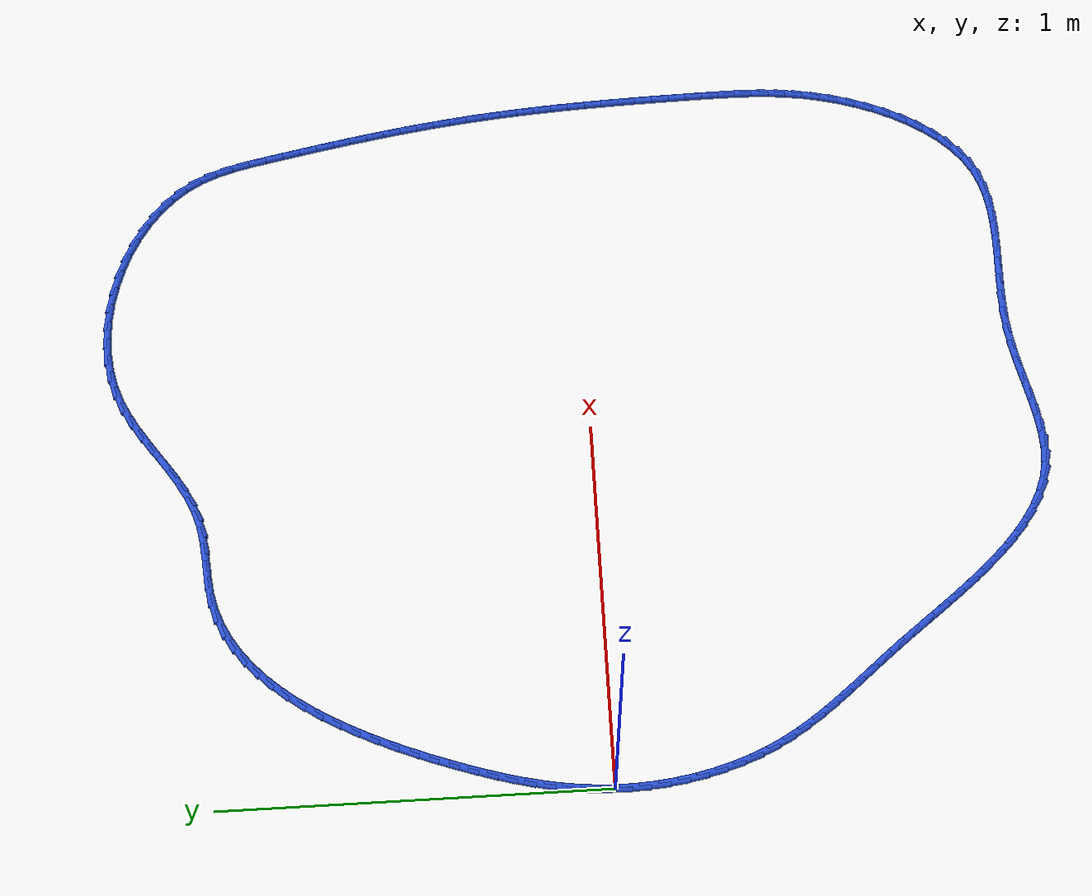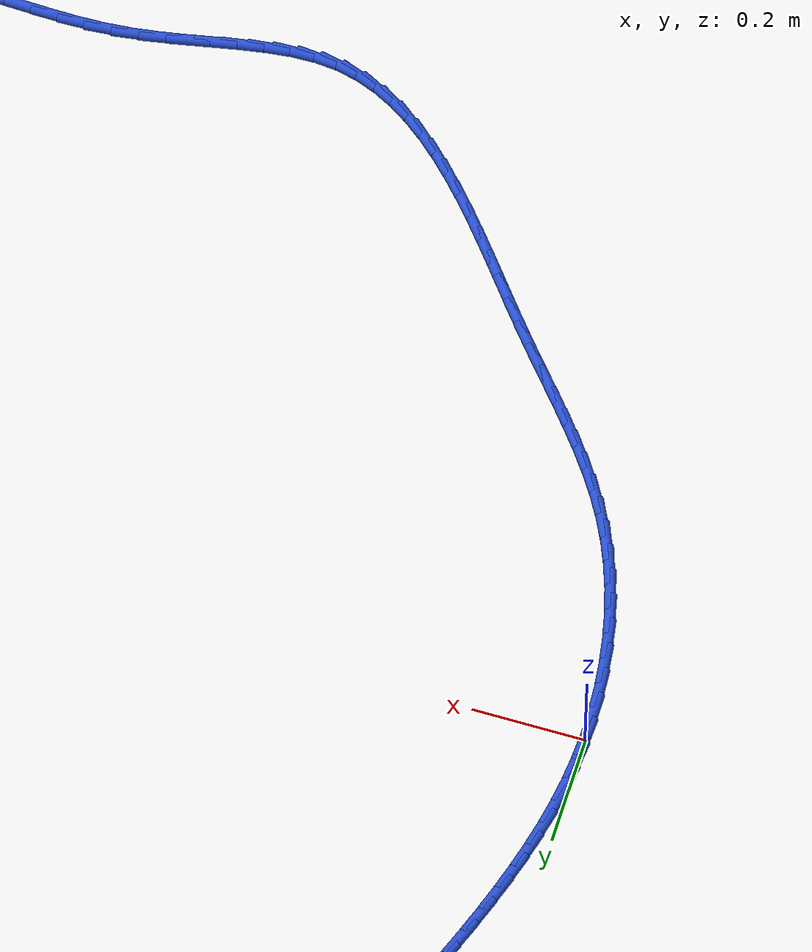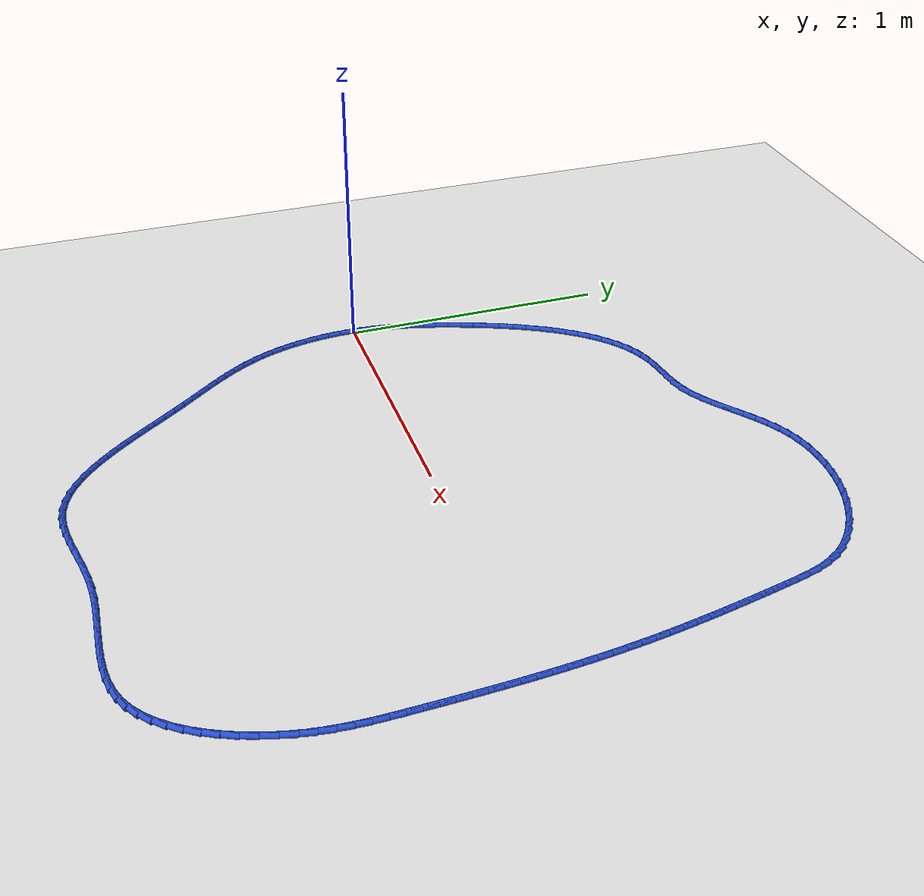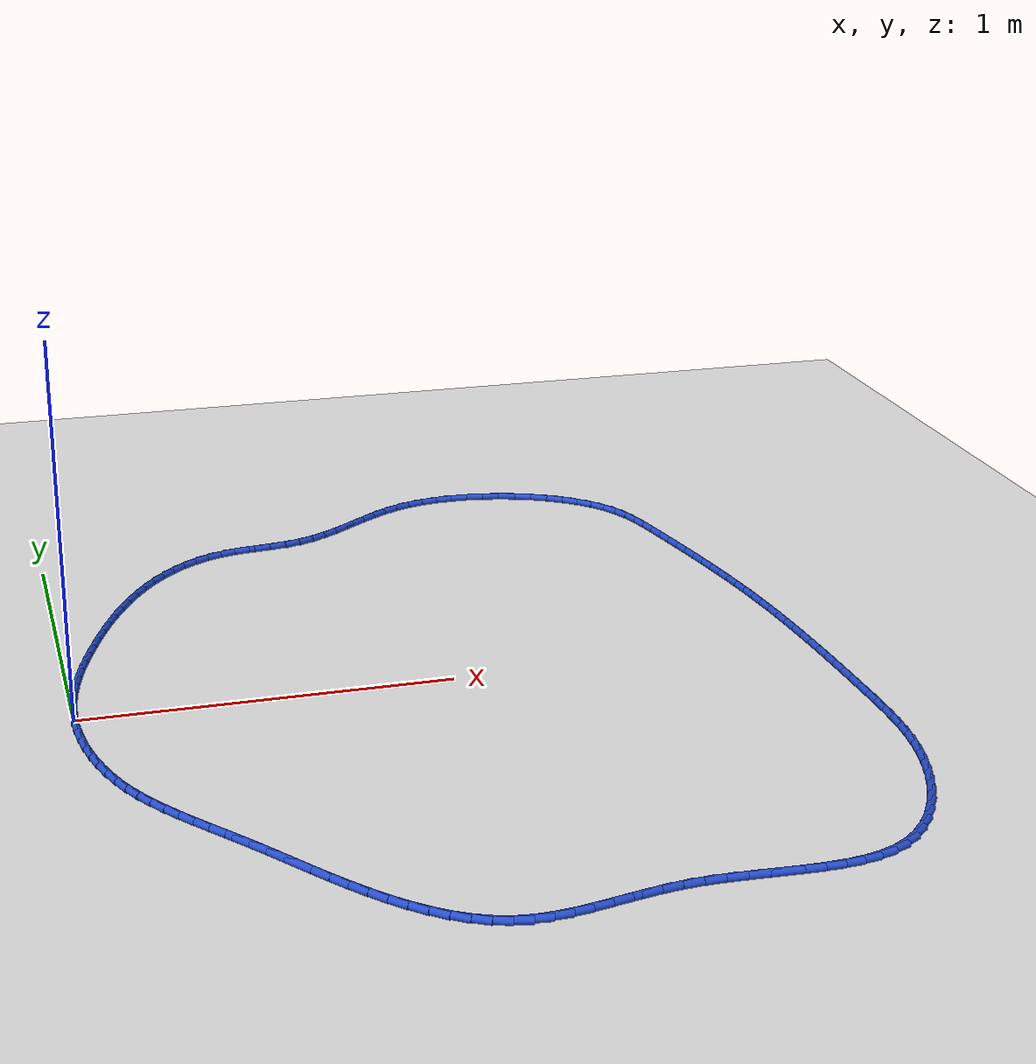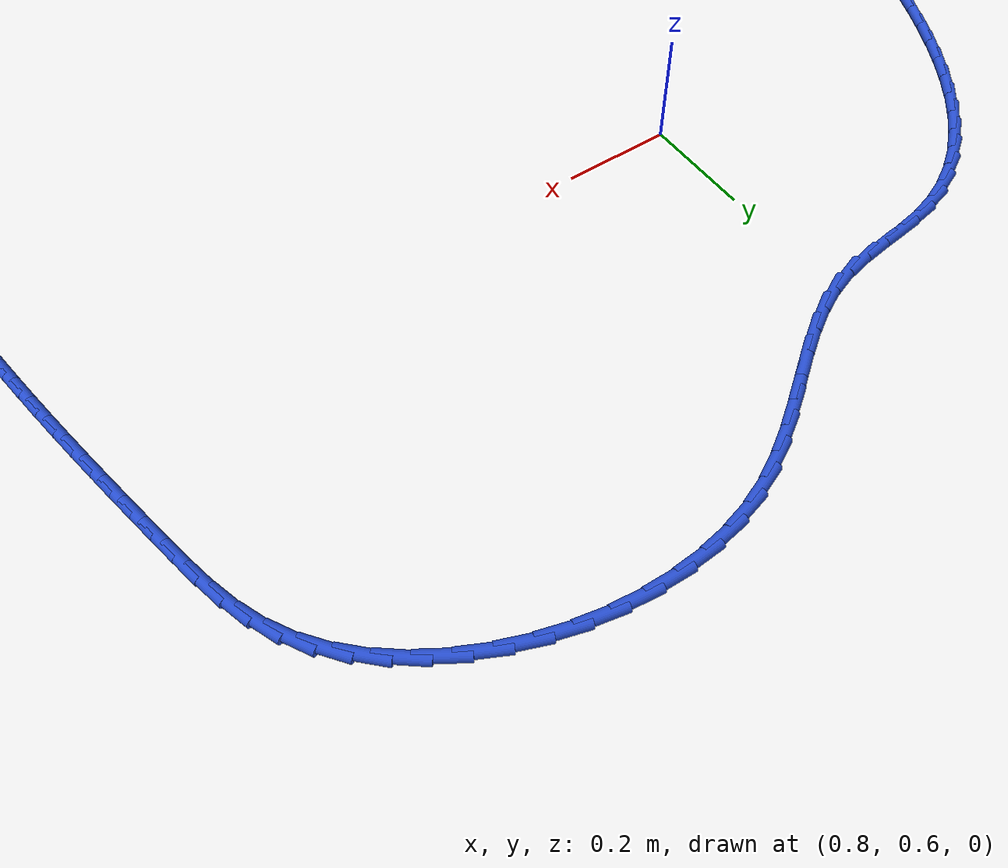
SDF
<sdf version="1.6">
 <world name="default">
  <light name="sun" type="directional">
   <pose>0 0 10 0 -0 0</pose>
   <diffuse>0.8 0.8 0.8 1</diffuse>
   <specular>0.2 0.2 0.2 1</specular>
   <attenuation>
    <range>1000</range>
    <constant>0.9</constant>
    <linear>0.01</linear>
    <quadratic>0.001</quadratic>
   </attenuation>
   <direction>-0.5 0.1 -0.9</direction>
  </light>
  <model name="ground_plane">
   <static>1</static>
   <link name="link">
    <collision name="collision">
     <geometry><plane><normal>0 0 1</normal><size>100 100</size></plane></geometry>
     <surface><friction><ode><mu>100</mu><mu2>50</mu2></ode></friction></surface>
    </collision>
    <visual name="visual">
     <cast_shadows>0</cast_shadows>
     <geometry><plane><normal>0 0 1</normal><size>100 100</size></plane></geometry>
     <material>
      <script><uri>file://media/materials/scripts/gazebo.material</uri><name>Gazebo/WhiteGlow</name></script>
     </material>
    </visual>
   </link>
  </model>
  <gravity>0 0 -9.8</gravity>
  <magnetic_field>6e-06 2.3e-05 -4.2e-05</magnetic_field>
  <atmosphere type="adiabatic"/>
  <physics name="default_physics" default="0" type="ode">
   <max_step_size>0.001</max_step_size>
   <real_time_factor>1</real_time_factor>
   <real_time_update_rate>1000</real_time_update_rate>
  </physics>
  <scene><ambient>0.4 0.4 0.4 1</ambient><background>0.7 0.7 0.7 1</background><shadows>1</shadows></scene>
  <spherical_coordinates>
   <surface_model>EARTH_WGS84</surface_model>
   <latitude_deg>0</latitude_deg>
   <longitude_deg>0</longitude_deg>
   <elevation>0</elevation>
   <heading_deg>0</heading_deg>
  </spherical_coordinates>
  <model name="line">
   <link name="link_0">
    <pose>2.949029909160572e-17 -9.71445146547012e-17 0.01 0 1.57 1.5242293871294126</pose>
    <collision name="collision">
     <geometry><cylinder><radius>0.01</radius><length>0.08</length></cylinder></geometry>
    </collision>
    <visual name="visual">
     <material>
      <script><name>Gazebo/Blue</name><uri>file://media/materials/scripts/gazebo.material</uri></script>
     </material>
     <geometry><cylinder><radius>0.01</radius><length>0.08</length></cylinder></geometry>
    </visual>
   </link>
   <link name="link_1">
    <pose>0.00221797405301965 0.047595367581147206 0.01 0 1.57 1.473411289266102</pose>
    <collision name="collision">
     <geometry><cylinder><radius>0.01</radius><length>0.08</length></cylinder></geometry>
    </collision>
    <visual name="visual">
     <material>
      <script><name>Gazebo/Blue</name><uri>file://media/materials/scripts/gazebo.material</uri></script>
     </material>
     <geometry><cylinder><radius>0.01</radius><length>0.08</length></cylinder></geometry>
    </visual>
   </link>
   <link name="link_2">
    <pose>0.0068180106514134425 0.09468150627326125 0.01 0 1.57 1.4257906642017169</pose>
    <collision name="collision">
     <geometry><cylinder><radius>0.01</radius><length>0.08</length></cylinder></geometry>
    </collision>
    <visual name="visual">
     <material>
      <script><name>Gazebo/Blue</name><uri>file://media/materials/scripts/gazebo.material</uri></script>
     </material>
     <geometry><cylinder><radius>0.01</radius><length>0.08</length></cylinder></geometry>
    </visual>
   </link>
   <link name="link_3">
    <pose>0.013643770705452916 0.1414234872267543 0.01 0 1.57 1.3820355925854608</pose>
    <collision name="collision">
     <geometry><cylinder><radius>0.01</radius><length>0.08</length></cylinder></geometry>
    </collision>
    <visual name="visual">
     <material>
      <script><name>Gazebo/Blue</name><uri>file://media/materials/scripts/gazebo.material</uri></script>
     </material>
     <geometry><cylinder><radius>0.01</radius><length>0.08</length></cylinder></geometry>
    </visual>
   </link>
   <link name="link_4">
    <pose>0.02253891512540955 0.18798638159203845 0.01 0 1.57 1.342648854685721</pose>
    <collision name="collision">
     <geometry><cylinder><radius>0.01</radius><length>0.08</length></cylinder></geometry>
    </collision>
    <visual name="visual">
     <material>
      <script><name>Gazebo/Blue</name><uri>file://media/materials/scripts/gazebo.material</uri></script>
     </material>
     <geometry><cylinder><radius>0.01</radius><length>0.08</length></cylinder></geometry>
    </visual>
   </link>
   <link name="link_5">
    <pose>0.03334710482155483 0.23453526051952595 0.01 0 1.57 1.3079645940863656</pose>
    <collision name="collision">
     <geometry><cylinder><radius>0.01</radius><length>0.08</length></cylinder></geometry>
    </collision>
    <visual name="visual">
     <material>
      <script><name>Gazebo/Blue</name><uri>file://media/materials/scripts/gazebo.material</uri></script>
     </material>
     <geometry><cylinder><radius>0.01</radius><length>0.08</length></cylinder></geometry>
    </visual>
   </link>
   <link name="link_6">
    <pose>0.04591200070416027 0.28123519515962897 0.01 0 1.57 1.2781604872505696</pose>
    <collision name="collision">
     <geometry><cylinder><radius>0.01</radius><length>0.08</length></cylinder></geometry>
    </collision>
    <visual name="visual">
     <material>
      <script><name>Gazebo/Blue</name><uri>file://media/materials/scripts/gazebo.material</uri></script>
     </material>
     <geometry><cylinder><radius>0.01</radius><length>0.08</length></cylinder></geometry>
    </visual>
   </link>
   <link name="link_7">
    <pose>0.06007726368349735 0.3282512566627597 0.01 0 1.57 1.2532796625277816</pose>
    <collision name="collision">
     <geometry><cylinder><radius>0.01</radius><length>0.08</length></cylinder></geometry>
    </collision>
    <visual name="visual">
     <material>
      <script><name>Gazebo/Blue</name><uri>file://media/materials/scripts/gazebo.material</uri></script>
     </material>
     <geometry><cylinder><radius>0.01</radius><length>0.08</length></cylinder></geometry>
    </visual>
   </link>
   <link name="link_8">
    <pose>0.07568655466983756 0.3757485161793304 0.01 0 1.57 1.2331978213480939</pose>
    <collision name="collision">
     <geometry><cylinder><radius>0.01</radius><length>0.08</length></cylinder></geometry>
    </collision>
    <visual name="visual">
     <material>
      <script><name>Gazebo/Blue</name><uri>file://media/materials/scripts/gazebo.material</uri></script>
     </material>
     <geometry><cylinder><radius>0.01</radius><length>0.08</length></cylinder></geometry>
    </visual>
   </link>
   <link name="link_9">
    <pose>0.09258527475787279 0.42388791957566047 0.01 0 1.57 1.2147229975062166</pose>
    <collision name="collision">
     <geometry><cylinder><radius>0.01</radius><length>0.08</length></cylinder></geometry>
    </collision>
    <visual name="visual">
     <material>
      <script><name>Gazebo/Blue</name><uri>file://media/materials/scripts/gazebo.material</uri></script>
     </material>
     <geometry><cylinder><radius>0.01</radius><length>0.08</length></cylinder></geometry>
    </visual>
   </link>
   <link name="link_10">
    <pose>0.11070888097141358 0.4726169259821213 0.01 0 1.57 1.1932077386899205</pose>
    <collision name="collision">
     <geometry><cylinder><radius>0.01</radius><length>0.08</length></cylinder></geometry>
    </collision>
    <visual name="visual">
     <material>
      <script><name>Gazebo/Blue</name><uri>file://media/materials/scripts/gazebo.material</uri></script>
     </material>
     <geometry><cylinder><radius>0.01</radius><length>0.08</length></cylinder></geometry>
    </visual>
   </link>
   <link name="link_11">
    <pose>0.13012473468402097 0.5215703018573088 0.01 0 1.57 1.1680369226061018</pose>
    <collision name="collision">
     <geometry><cylinder><radius>0.01</radius><length>0.08</length></cylinder></geometry>
    </collision>
    <visual name="visual">
     <material>
      <script><name>Gazebo/Blue</name><uri>file://media/materials/scripts/gazebo.material</uri></script>
     </material>
     <geometry><cylinder><radius>0.01</radius><length>0.08</length></cylinder></geometry>
    </visual>
   </link>
   <link name="link_12">
    <pose>0.150910691181727 0.5703579367733892 0.01 0 1.57 1.1388485776382675</pose>
    <collision name="collision">
     <geometry><cylinder><radius>0.01</radius><length>0.08</length></cylinder></geometry>
    </collision>
    <visual name="visual">
     <material>
      <script><name>Gazebo/Blue</name><uri>file://media/materials/scripts/gazebo.material</uri></script>
     </material>
     <geometry><cylinder><radius>0.01</radius><length>0.08</length></cylinder></geometry>
    </visual>
   </link>
   <link name="link_13">
    <pose>0.17314460575056412 0.6185897203025308 0.01 0 1.57 1.1051743146297641</pose>
    <collision name="collision">
     <geometry><cylinder><radius>0.01</radius><length>0.08</length></cylinder></geometry>
    </collision>
    <visual name="visual">
     <material>
      <script><name>Gazebo/Blue</name><uri>file://media/materials/scripts/gazebo.material</uri></script>
     </material>
     <geometry><cylinder><radius>0.01</radius><length>0.08</length></cylinder></geometry>
    </visual>
   </link>
   <link name="link_14">
    <pose>0.19690433367656446 0.6658755420169 0.01 0 1.57 1.0664333350519362</pose>
    <collision name="collision">
     <geometry><cylinder><radius>0.01</radius><length>0.08</length></cylinder></geometry>
    </collision>
    <visual name="visual">
     <material>
      <script><name>Gazebo/Blue</name><uri>file://media/materials/scripts/gazebo.material</uri></script>
     </material>
     <geometry><cylinder><radius>0.01</radius><length>0.08</length></cylinder></geometry>
    </visual>
   </link>
   <link name="link_15">
    <pose>0.22226773024576033 0.7118252914886641 0.01 0 1.57 1.0219274654599304</pose>
    <collision name="collision">
     <geometry><cylinder><radius>0.01</radius><length>0.08</length></cylinder></geometry>
    </collision>
    <visual name="visual">
     <material>
      <script><name>Gazebo/Blue</name><uri>file://media/materials/scripts/gazebo.material</uri></script>
     </material>
     <geometry><cylinder><radius>0.01</radius><length>0.08</length></cylinder></geometry>
    </visual>
   </link>
   <link name="link_16">
    <pose>0.24931265074418407 0.7560488582899912 0.01 0 1.57 0.9708422088777604</pose>
    <collision name="collision">
     <geometry><cylinder><radius>0.01</radius><length>0.08</length></cylinder></geometry>
    </collision>
    <visual name="visual">
     <material>
      <script><name>Gazebo/Blue</name><uri>file://media/materials/scripts/gazebo.material</uri></script>
     </material>
     <geometry><cylinder><radius>0.01</radius><length>0.08</length></cylinder></geometry>
    </visual>
   </link>
   <link name="link_17">
    <pose>0.27811695045786783 0.7981561319930478 0.01 0 1.57 0.9122619753968884</pose>
    <collision name="collision">
     <geometry><cylinder><radius>0.01</radius><length>0.08</length></cylinder></geometry>
    </collision>
    <visual name="visual">
     <material>
      <script><name>Gazebo/Blue</name><uri>file://media/materials/scripts/gazebo.material</uri></script>
     </material>
     <geometry><cylinder><radius>0.01</radius><length>0.08</length></cylinder></geometry>
    </visual>
   </link>
   <link name="link_18">
    <pose>0.3087584846728439 0.8377570021700012 0.01 0 1.57 0.845212282976439</pose>
    <collision name="collision">
     <geometry><cylinder><radius>0.01</radius><length>0.08</length></cylinder></geometry>
    </collision>
    <visual name="visual">
     <material>
      <script><name>Gazebo/Blue</name><uri>file://media/materials/scripts/gazebo.material</uri></script>
     </material>
     <geometry><cylinder><radius>0.01</radius><length>0.08</length></cylinder></geometry>
    </visual>
   </link>
   <link name="link_19">
    <pose>0.3413151086751447 0.8744613583930186 0.01 0 1.57 0.7687470295034691</pose>
    <collision name="collision">
     <geometry><cylinder><radius>0.01</radius><length>0.08</length></cylinder></geometry>
    </collision>
    <visual name="visual">
     <material>
      <script><name>Gazebo/Blue</name><uri>file://media/materials/scripts/gazebo.material</uri></script>
     </material>
     <geometry><cylinder><radius>0.01</radius><length>0.08</length></cylinder></geometry>
    </visual>
   </link>
   <link name="link_20">
    <pose>0.3758646777508022 0.9078790902342675 0.01 0 1.57 0.6821018119404471</pose>
    <collision name="collision">
     <geometry><cylinder><radius>0.01</radius><length>0.08</length></cylinder></geometry>
    </collision>
    <visual name="visual">
     <material>
      <script><name>Gazebo/Blue</name><uri>file://media/materials/scripts/gazebo.material</uri></script>
     </material>
     <geometry><cylinder><radius>0.01</radius><length>0.08</length></cylinder></geometry>
    </visual>
   </link>
   <link name="link_21">
    <pose>0.412485047185849 0.9376200872659153 0.01 0 1.57 0.5849272882402394</pose>
    <collision name="collision">
     <geometry><cylinder><radius>0.01</radius><length>0.08</length></cylinder></geometry>
    </collision>
    <visual name="visual">
     <material>
      <script><name>Gazebo/Blue</name><uri>file://media/materials/scripts/gazebo.material</uri></script>
     </material>
     <geometry><cylinder><radius>0.01</radius><length>0.08</length></cylinder></geometry>
    </visual>
   </link>
   <link name="link_22">
    <pose>0.45125407226631703 0.9632942390601287 0.01 0 1.57 0.4775879944381283</pose>
    <collision name="collision">
     <geometry><cylinder><radius>0.01</radius><length>0.08</length></cylinder></geometry>
    </collision>
    <visual name="visual">
     <material>
      <script><name>Gazebo/Blue</name><uri>file://media/materials/scripts/gazebo.material</uri></script>
     </material>
     <geometry><cylinder><radius>0.01</radius><length>0.08</length></cylinder></geometry>
    </visual>
   </link>
   <link name="link_23">
    <pose>0.49224960827823894 0.9845114351890756 0.01 0 1.57 0.36145412227707635</pose>
    <collision name="collision">
     <geometry><cylinder><radius>0.01</radius><length>0.08</length></cylinder></geometry>
    </collision>
    <visual name="visual">
     <material>
      <script><name>Gazebo/Blue</name><uri>file://media/materials/scripts/gazebo.material</uri></script>
     </material>
     <geometry><cylinder><radius>0.01</radius><length>0.08</length></cylinder></geometry>
    </visual>
   </link>
   <link name="link_24">
    <pose>0.5355495105076465 1.0008815652249223 0.01 0 1.57 0.23987250766087118</pose>
    <collision name="collision">
     <geometry><cylinder><radius>0.01</radius><length>0.08</length></cylinder></geometry>
    </collision>
    <visual name="visual">
     <material>
      <script><name>Gazebo/Blue</name><uri>file://media/materials/scripts/gazebo.material</uri></script>
     </material>
     <geometry><cylinder><radius>0.01</radius><length>0.08</length></cylinder></geometry>
    </visual>
   </link>
   <link name="link_25">
    <pose>0.581217037028305 1.012051000995506 0.01 0 1.57 0.14384823755635906</pose>
    <collision name="collision">
     <geometry><cylinder><radius>0.01</radius><length>0.08</length></cylinder></geometry>
    </collision>
    <visual name="visual">
     <material>
      <script><name>Gazebo/Blue</name><uri>file://media/materials/scripts/gazebo.material</uri></script>
     </material>
     <geometry><cylinder><radius>0.01</radius><length>0.08</length></cylinder></geometry>
    </visual>
   </link>
   <link name="link_26">
    <pose>0.6288041666725926 1.0189439350289768 0.01 0 1.57 0.10541199539217004</pose>
    <collision name="collision">
     <geometry><cylinder><radius>0.01</radius><length>0.08</length></cylinder></geometry>
    </collision>
    <visual name="visual">
     <material>
      <script><name>Gazebo/Blue</name><uri>file://media/materials/scripts/gazebo.material</uri></script>
     </material>
     <geometry><cylinder><radius>0.01</radius><length>0.08</length></cylinder></geometry>
    </visual>
   </link>
   <link name="link_27">
    <pose>0.6772295002293567 1.0240675374313675 0.01 0 1.57 0.12316833886986119</pose>
    <collision name="collision">
     <geometry><cylinder><radius>0.01</radius><length>0.08</length></cylinder></geometry>
    </collision>
    <visual name="visual">
     <material>
      <script><name>Gazebo/Blue</name><uri>file://media/materials/scripts/gazebo.material</uri></script>
     </material>
     <geometry><cylinder><radius>0.01</radius><length>0.08</length></cylinder></geometry>
    </visual>
   </link>
   <link name="link_28">
    <pose>0.7253722699110264 1.0300273706896552 0.01 0 1.57 0.19850085061616227</pose>
    <collision name="collision">
     <geometry><cylinder><radius>0.01</radius><length>0.08</length></cylinder></geometry>
    </collision>
    <visual name="visual">
     <material>
      <script><name>Gazebo/Blue</name><uri>file://media/materials/scripts/gazebo.material</uri></script>
     </material>
     <geometry><cylinder><radius>0.01</radius><length>0.08</length></cylinder></geometry>
    </visual>
   </link>
   <link name="link_29">
    <pose>0.772111707930032 1.0394289972908177 0.01 0 1.57 0.3248334006243878</pose>
    <collision name="collision">
     <geometry><cylinder><radius>0.01</radius><length>0.08</length></cylinder></geometry>
    </collision>
    <visual name="visual">
     <material>
      <script><name>Gazebo/Blue</name><uri>file://media/materials/scripts/gazebo.material</uri></script>
     </material>
     <geometry><cylinder><radius>0.01</radius><length>0.08</length></cylinder></geometry>
    </visual>
   </link>
   <link name="link_30">
    <pose>0.8165432968133 1.054391879245468 0.01 0 1.57 0.4434501307316704</pose>
    <collision name="collision">
     <geometry><cylinder><radius>0.01</radius><length>0.08</length></cylinder></geometry>
    </collision>
    <visual name="visual">
     <material>
      <script><name>Gazebo/Blue</name><uri>file://media/materials/scripts/gazebo.material</uri></script>
     </material>
     <geometry><cylinder><radius>0.01</radius><length>0.08</length></cylinder></geometry>
    </visual>
   </link>
   <link name="link_31">
    <pose>0.8588879443335512 1.0745056799400492 0.01 0 1.57 0.5318767649467564</pose>
    <collision name="collision">
     <geometry><cylinder><radius>0.01</radius><length>0.08</length></cylinder></geometry>
    </collision>
    <visual name="visual">
     <material>
      <script><name>Gazebo/Blue</name><uri>file://media/materials/scripts/gazebo.material</uri></script>
     </material>
     <geometry><cylinder><radius>0.01</radius><length>0.08</length></cylinder></geometry>
    </visual>
   </link>
   <link name="link_32">
    <pose>0.8997315099883101 1.0985397023019257 0.01 0 1.57 0.5898053700524903</pose>
    <collision name="collision">
     <geometry><cylinder><radius>0.01</radius><length>0.08</length></cylinder></geometry>
    </collision>
    <visual name="visual">
     <material>
      <script><name>Gazebo/Blue</name><uri>file://media/materials/scripts/gazebo.material</uri></script>
     </material>
     <geometry><cylinder><radius>0.01</radius><length>0.08</length></cylinder></geometry>
    </visual>
   </link>
   <link name="link_33">
    <pose>0.9396600428311411 1.1252628231629824 0.01 0 1.57 0.6185033312914714</pose>
    <collision name="collision">
     <geometry><cylinder><radius>0.01</radius><length>0.08</length></cylinder></geometry>
    </collision>
    <visual name="visual">
     <material>
      <script><name>Gazebo/Blue</name><uri>file://media/materials/scripts/gazebo.material</uri></script>
     </material>
     <geometry><cylinder><radius>0.01</radius><length>0.08</length></cylinder></geometry>
    </visual>
   </link>
   <link name="link_34">
    <pose>0.9792595919156093 1.1534439193551038 0.01 0 1.57 0.6192342919781912</pose>
    <collision name="collision">
     <geometry><cylinder><radius>0.01</radius><length>0.08</length></cylinder></geometry>
    </collision>
    <visual name="visual">
     <material>
      <script><name>Gazebo/Blue</name><uri>file://media/materials/scripts/gazebo.material</uri></script>
     </material>
     <geometry><cylinder><radius>0.01</radius><length>0.08</length></cylinder></geometry>
    </visual>
   </link>
   <link name="link_35">
    <pose>1.019116206295279 1.1818518677101748 0.01 0 1.57 0.5925901608837325</pose>
    <collision name="collision">
     <geometry><cylinder><radius>0.01</radius><length>0.08</length></cylinder></geometry>
    </collision>
    <visual name="visual">
     <material>
      <script><name>Gazebo/Blue</name><uri>file://media/materials/scripts/gazebo.material</uri></script>
     </material>
     <geometry><cylinder><radius>0.01</radius><length>0.08</length></cylinder></geometry>
    </visual>
   </link>
   <link name="link_36">
    <pose>1.0598159350237153 1.2092555450600795 0.01 0 1.57 0.5385139920976149</pose>
    <collision name="collision">
     <geometry><cylinder><radius>0.01</radius><length>0.08</length></cylinder></geometry>
    </collision>
    <visual name="visual">
     <material>
      <script><name>Gazebo/Blue</name><uri>file://media/materials/scripts/gazebo.material</uri></script>
     </material>
     <geometry><cylinder><radius>0.01</radius><length>0.08</length></cylinder></geometry>
    </visual>
   </link>
   <link name="link_37">
    <pose>1.101944827154482 1.2344238282367026 0.01 0 1.57 0.4569146160596602</pose>
    <collision name="collision">
     <geometry><cylinder><radius>0.01</radius><length>0.08</length></cylinder></geometry>
    </collision>
    <visual name="visual">
     <material>
      <script><name>Gazebo/Blue</name><uri>file://media/materials/scripts/gazebo.material</uri></script>
     </material>
     <geometry><cylinder><radius>0.01</radius><length>0.08</length></cylinder></geometry>
    </visual>
   </link>
   <link name="link_38">
    <pose>1.146088931741145 1.2561255940719298 0.01 0 1.57 0.34975207894453036</pose>
    <collision name="collision">
     <geometry><cylinder><radius>0.01</radius><length>0.08</length></cylinder></geometry>
    </collision>
    <visual name="visual">
     <material>
      <script><name>Gazebo/Blue</name><uri>file://media/materials/scripts/gazebo.material</uri></script>
     </material>
     <geometry><cylinder><radius>0.01</radius><length>0.08</length></cylinder></geometry>
    </visual>
   </link>
   <link name="link_39">
    <pose>1.1928035203747764 1.2731646265144851 0.01 0 1.57 0.2366582090059286</pose>
    <collision name="collision">
     <geometry><cylinder><radius>0.01</radius><length>0.08</length></cylinder></geometry>
    </collision>
    <visual name="visual">
     <material>
      <script><name>Gazebo/Blue</name><uri>file://media/materials/scripts/gazebo.material</uri></script>
     </material>
     <geometry><cylinder><radius>0.01</radius><length>0.08</length></cylinder></geometry>
    </visual>
   </link>
   <link name="link_40">
    <pose>1.2420328990798146 1.2850376531378502 0.01 0 1.57 0.1330069167161616</pose>
    <collision name="collision">
     <geometry><cylinder><radius>0.01</radius><length>0.08</length></cylinder></geometry>
    </collision>
    <visual name="visual">
     <material>
      <script><name>Gazebo/Blue</name><uri>file://media/materials/scripts/gazebo.material</uri></script>
     </material>
     <geometry><cylinder><radius>0.01</radius><length>0.08</length></cylinder></geometry>
    </visual>
   </link>
   <link name="link_41">
    <pose>1.2931598435172316 1.2918782768268497 0.01 0 1.57 0.03750152560459104</pose>
    <collision name="collision">
     <geometry><cylinder><radius>0.01</radius><length>0.08</length></cylinder></geometry>
    </collision>
    <visual name="visual">
     <material>
      <script><name>Gazebo/Blue</name><uri>file://media/materials/scripts/gazebo.material</uri></script>
     </material>
     <geometry><cylinder><radius>0.01</radius><length>0.08</length></cylinder></geometry>
    </visual>
   </link>
   <link name="link_42">
    <pose>1.345546260996247 1.2938437688890414 0.01 0 1.57 -0.05187724870338346</pose>
    <collision name="collision">
     <geometry><cylinder><radius>0.01</radius><length>0.08</length></cylinder></geometry>
    </collision>
    <visual name="visual">
     <material>
      <script><name>Gazebo/Blue</name><uri>file://media/materials/scripts/gazebo.material</uri></script>
     </material>
     <geometry><cylinder><radius>0.01</radius><length>0.08</length></cylinder></geometry>
    </visual>
   </link>
   <link name="link_43">
    <pose>1.3985540588260812 1.2910914006319811 0.01 0 1.57 -0.137137323295058</pose>
    <collision name="collision">
     <geometry><cylinder><radius>0.01</radius><length>0.08</length></cylinder></geometry>
    </collision>
    <visual name="visual">
     <material>
      <script><name>Gazebo/Blue</name><uri>file://media/materials/scripts/gazebo.material</uri></script>
     </material>
     <geometry><cylinder><radius>0.01</radius><length>0.08</length></cylinder></geometry>
    </visual>
   </link>
   <link name="link_44">
    <pose>1.4515451443159546 1.2837784433632267 0.01 0 1.57 -0.22023411728320377</pose>
    <collision name="collision">
     <geometry><cylinder><radius>0.01</radius><length>0.08</length></cylinder></geometry>
    </collision>
    <visual name="visual">
     <material>
      <script><name>Gazebo/Blue</name><uri>file://media/materials/scripts/gazebo.material</uri></script>
     </material>
     <geometry><cylinder><radius>0.01</radius><length>0.08</length></cylinder></geometry>
    </visual>
   </link>
   <link name="link_45">
    <pose>1.5038814247750873 1.2720621683903344 0.01 0 1.57 -0.30308590247316947</pose>
    <collision name="collision">
     <geometry><cylinder><radius>0.01</radius><length>0.08</length></cylinder></geometry>
    </collision>
    <visual name="visual">
     <material>
      <script><name>Gazebo/Blue</name><uri>file://media/materials/scripts/gazebo.material</uri></script>
     </material>
     <geometry><cylinder><radius>0.01</radius><length>0.08</length></cylinder></geometry>
    </visual>
   </link>
   <link name="link_46">
    <pose>1.554924807512699 1.2560998470208609 0.01 0 1.57 -0.3876149464044524</pose>
    <collision name="collision">
     <geometry><cylinder><radius>0.01</radius><length>0.08</length></cylinder></geometry>
    </collision>
    <visual name="visual">
     <material>
      <script><name>Gazebo/Blue</name><uri>file://media/materials/scripts/gazebo.material</uri></script>
     </material>
     <geometry><cylinder><radius>0.01</radius><length>0.08</length></cylinder></geometry>
    </visual>
   </link>
   <link name="link_47">
    <pose>1.60403719983801 1.2360487505623643 0.01 0 1.57 -0.4757927429763021</pose>
    <collision name="collision">
     <geometry><cylinder><radius>0.01</radius><length>0.08</length></cylinder></geometry>
    </collision>
    <visual name="visual">
     <material>
      <script><name>Gazebo/Blue</name><uri>file://media/materials/scripts/gazebo.material</uri></script>
     </material>
     <geometry><cylinder><radius>0.01</radius><length>0.08</length></cylinder></geometry>
    </visual>
   </link>
   <link name="link_48">
    <pose>1.6505805090602406 1.2120661503224 0.01 0 1.57 -0.5696684634232014</pose>
    <collision name="collision">
     <geometry><cylinder><radius>0.01</radius><length>0.08</length></cylinder></geometry>
    </collision>
    <visual name="visual">
     <material>
      <script><name>Gazebo/Blue</name><uri>file://media/materials/scripts/gazebo.material</uri></script>
     </material>
     <geometry><cylinder><radius>0.01</radius><length>0.08</length></cylinder></geometry>
    </visual>
   </link>
   <link name="link_49">
    <pose>1.6939166424886103 1.1843093176085253 0.01 0 1.57 -0.6713519102458148</pose>
    <collision name="collision">
     <geometry><cylinder><radius>0.01</radius><length>0.08</length></cylinder></geometry>
    </collision>
    <visual name="visual">
     <material>
      <script><name>Gazebo/Blue</name><uri>file://media/materials/scripts/gazebo.material</uri></script>
     </material>
     <geometry><cylinder><radius>0.01</radius><length>0.08</length></cylinder></geometry>
    </visual>
   </link>
   <link name="link_50">
    <pose>1.73340750743234 1.1529355237282974 0.01 0 1.57 -0.7829065080619406</pose>
    <collision name="collision">
     <geometry><cylinder><radius>0.01</radius><length>0.08</length></cylinder></geometry>
    </collision>
    <visual name="visual">
     <material>
      <script><name>Gazebo/Blue</name><uri>file://media/materials/scripts/gazebo.material</uri></script>
     </material>
     <geometry><cylinder><radius>0.01</radius><length>0.08</length></cylinder></geometry>
    </visual>
   </link>
   <link name="link_51">
    <pose>1.7684150112006496 1.1181020399892734 0.01 0 1.57 -0.9060909009477038</pose>
    <collision name="collision">
     <geometry><cylinder><radius>0.01</radius><length>0.08</length></cylinder></geometry>
    </collision>
    <visual name="visual">
     <material>
      <script><name>Gazebo/Blue</name><uri>file://media/materials/scripts/gazebo.material</uri></script>
     </material>
     <geometry><cylinder><radius>0.01</radius><length>0.08</length></cylinder></geometry>
    </visual>
   </link>
   <link name="link_52">
    <pose>1.7983010611027588 1.0799661376990095 0.01 0 1.57 -1.0411979860862466</pose>
    <collision name="collision">
     <geometry><cylinder><radius>0.01</radius><length>0.08</length></cylinder></geometry>
    </collision>
    <visual name="visual">
     <material>
      <script><name>Gazebo/Blue</name><uri>file://media/materials/scripts/gazebo.material</uri></script>
     </material>
     <geometry><cylinder><radius>0.01</radius><length>0.08</length></cylinder></geometry>
    </visual>
   </link>
   <link name="link_53">
    <pose>1.8224604310953054 1.038694708180517 0.01 0 1.57 -1.1679520217540105</pose>
    <collision name="collision">
     <geometry><cylinder><radius>0.01</radius><length>0.08</length></cylinder></geometry>
    </collision>
    <visual name="visual">
     <material>
      <script><name>Gazebo/Blue</name><uri>file://media/materials/scripts/gazebo.material</uri></script>
     </material>
     <geometry><cylinder><radius>0.01</radius><length>0.08</length></cylinder></geometry>
    </visual>
   </link>
   <link name="link_54">
    <pose>1.8411996132791808 0.9947215012083546 0.01 0 1.57 -1.2624683397445804</pose>
    <collision name="collision">
     <geometry><cylinder><radius>0.01</radius><length>0.08</length></cylinder></geometry>
    </collision>
    <visual name="visual">
     <material>
      <script><name>Gazebo/Blue</name><uri>file://media/materials/scripts/gazebo.material</uri></script>
     </material>
     <geometry><cylinder><radius>0.01</radius><length>0.08</length></cylinder></geometry>
    </visual>
   </link>
   <link name="link_55">
    <pose>1.8558328100688124 0.9487752217639905 0.01 0 1.57 -1.3238297464606992</pose>
    <collision name="collision">
     <geometry><cylinder><radius>0.01</radius><length>0.08</length></cylinder></geometry>
    </collision>
    <visual name="visual">
     <material>
      <script><name>Gazebo/Blue</name><uri>file://media/materials/scripts/gazebo.material</uri></script>
     </material>
     <geometry><cylinder><radius>0.01</radius><length>0.08</length></cylinder></geometry>
    </visual>
   </link>
   <link name="link_56">
    <pose>1.8677263492898408 0.9015998318538947 0.01 0 1.57 -1.3535588076388507</pose>
    <collision name="collision">
     <geometry><cylinder><radius>0.01</radius><length>0.08</length></cylinder></geometry>
    </collision>
    <visual name="visual">
     <material>
      <script><name>Gazebo/Blue</name><uri>file://media/materials/scripts/gazebo.material</uri></script>
     </material>
     <geometry><cylinder><radius>0.01</radius><length>0.08</length></cylinder></geometry>
    </visual>
   </link>
   <link name="link_57">
    <pose>1.8782460705761206 0.8539390243458698 0.01 0 1.57 -1.3600616770433782</pose>
    <collision name="collision">
     <geometry><cylinder><radius>0.01</radius><length>0.08</length></cylinder></geometry>
    </collision>
    <visual name="visual">
     <material>
      <script><name>Gazebo/Blue</name><uri>file://media/materials/scripts/gazebo.material</uri></script>
     </material>
     <geometry><cylinder><radius>0.01</radius><length>0.08</length></cylinder></geometry>
    </visual>
   </link>
   <link name="link_58">
    <pose>1.8884251988642933 0.8063531226225019 0.01 0 1.57 -1.363895592016477</pose>
    <collision name="collision">
     <geometry><cylinder><radius>0.01</radius><length>0.08</length></cylinder></geometry>
    </collision>
    <visual name="visual">
     <material>
      <script><name>Gazebo/Blue</name><uri>file://media/materials/scripts/gazebo.material</uri></script>
     </material>
     <geometry><cylinder><radius>0.01</radius><length>0.08</length></cylinder></geometry>
    </visual>
   </link>
   <link name="link_59">
    <pose>1.8983857962504922 0.7589001287245609 0.01 0 1.57 -1.3685308264803924</pose>
    <collision name="collision">
     <geometry><cylinder><radius>0.01</radius><length>0.08</length></cylinder></geometry>
    </collision>
    <visual name="visual">
     <material>
      <script><name>Gazebo/Blue</name><uri>file://media/materials/scripts/gazebo.material</uri></script>
     </material>
     <geometry><cylinder><radius>0.01</radius><length>0.08</length></cylinder></geometry>
    </visual>
   </link>
   <link name="link_60">
    <pose>1.908095299466066 0.71155280019286 0.01 0 1.57 -1.373969089016939</pose>
    <collision name="collision">
     <geometry><cylinder><radius>0.01</radius><length>0.08</length></cylinder></geometry>
    </collision>
    <visual name="visual">
     <material>
      <script><name>Gazebo/Blue</name><uri>file://media/materials/scripts/gazebo.material</uri></script>
     </material>
     <geometry><cylinder><radius>0.01</radius><length>0.08</length></cylinder></geometry>
    </visual>
   </link>
   <link name="link_61">
    <pose>1.9175211452423655 0.6642838945682128 0.01 0 1.57 -1.3802098450093578</pose>
    <collision name="collision">
     <geometry><cylinder><radius>0.01</radius><length>0.08</length></cylinder></geometry>
    </collision>
    <visual name="visual">
     <material>
      <script><name>Gazebo/Blue</name><uri>file://media/materials/scripts/gazebo.material</uri></script>
     </material>
     <geometry><cylinder><radius>0.01</radius><length>0.08</length></cylinder></geometry>
    </visual>
   </link>
   <link name="link_62">
    <pose>1.9266307703107397 0.6170661693914327 0.01 0 1.57 -1.3872501850786234</pose>
    <collision name="collision">
     <geometry><cylinder><radius>0.01</radius><length>0.08</length></cylinder></geometry>
    </collision>
    <visual name="visual">
     <material>
      <script><name>Gazebo/Blue</name><uri>file://media/materials/scripts/gazebo.material</uri></script>
     </material>
     <geometry><cylinder><radius>0.01</radius><length>0.08</length></cylinder></geometry>
    </visual>
   </link>
   <link name="link_63">
    <pose>1.9353916114025382 0.569872382203334 0.01 0 1.57 -1.3950846939514612</pose>
    <collision name="collision">
     <geometry><cylinder><radius>0.01</radius><length>0.08</length></cylinder></geometry>
    </collision>
    <visual name="visual">
     <material>
      <script><name>Gazebo/Blue</name><uri>file://media/materials/scripts/gazebo.material</uri></script>
     </material>
     <geometry><cylinder><radius>0.01</radius><length>0.08</length></cylinder></geometry>
    </visual>
   </link>
   <link name="link_64">
    <pose>1.9437711052491107 0.5226752905447302 0.01 0 1.57 -1.403705322986966</pose>
    <collision name="collision">
     <geometry><cylinder><radius>0.01</radius><length>0.08</length></cylinder></geometry>
    </collision>
    <visual name="visual">
     <material>
      <script><name>Gazebo/Blue</name><uri>file://media/materials/scripts/gazebo.material</uri></script>
     </material>
     <geometry><cylinder><radius>0.01</radius><length>0.08</length></cylinder></geometry>
    </visual>
   </link>
   <link name="link_65">
    <pose>1.9517366885818068 0.47544765195643496 0.01 0 1.57 -1.4131012701373682</pose>
    <collision name="collision">
     <geometry><cylinder><radius>0.01</radius><length>0.08</length></cylinder></geometry>
    </collision>
    <visual name="visual">
     <material>
      <script><name>Gazebo/Blue</name><uri>file://media/materials/scripts/gazebo.material</uri></script>
     </material>
     <geometry><cylinder><radius>0.01</radius><length>0.08</length></cylinder></geometry>
    </visual>
   </link>
   <link name="link_66">
    <pose>1.9592557981319767 0.42816222397926196 0.01 0 1.57 -1.4232588716117494</pose>
    <collision name="collision">
     <geometry><cylinder><radius>0.01</radius><length>0.08</length></cylinder></geometry>
    </collision>
    <visual name="visual">
     <material>
      <script><name>Gazebo/Blue</name><uri>file://media/materials/scripts/gazebo.material</uri></script>
     </material>
     <geometry><cylinder><radius>0.01</radius><length>0.08</length></cylinder></geometry>
    </visual>
   </link>
   <link name="link_67">
    <pose>1.9662958706309694 0.3807917641540243 0.01 0 1.57 -1.4341615099160814</pose>
    <collision name="collision">
     <geometry><cylinder><radius>0.01</radius><length>0.08</length></cylinder></geometry>
    </collision>
    <visual name="visual">
     <material>
      <script><name>Gazebo/Blue</name><uri>file://media/materials/scripts/gazebo.material</uri></script>
     </material>
     <geometry><cylinder><radius>0.01</radius><length>0.08</length></cylinder></geometry>
    </visual>
   </link>
   <link name="link_68">
    <pose>1.9728243428101344 0.3333090300215366 0.01 0 1.57 -1.4457895019869569</pose>
    <collision name="collision">
     <geometry><cylinder><radius>0.01</radius><length>0.08</length></cylinder></geometry>
    </collision>
    <visual name="visual">
     <material>
      <script><name>Gazebo/Blue</name><uri>file://media/materials/scripts/gazebo.material</uri></script>
     </material>
     <geometry><cylinder><radius>0.01</radius><length>0.08</length></cylinder></geometry>
    </visual>
   </link>
   <link name="link_69">
    <pose>1.978808653214574 0.285686780562777 0.01 0 1.57 -1.457825893301726</pose>
    <collision name="collision">
     <geometry><cylinder><radius>0.01</radius><length>0.08</length></cylinder></geometry>
    </collision>
    <visual name="visual">
     <material>
      <script><name>Gazebo/Blue</name><uri>file://media/materials/scripts/gazebo.material</uri></script>
     </material>
     <geometry><cylinder><radius>0.01</radius><length>0.08</length></cylinder></geometry>
    </visual>
   </link>
   <link name="link_70">
    <pose>1.9842293056223346 0.23790814888400266 0.01 0 1.57 -1.4692637544936353</pose>
    <collision name="collision">
     <geometry><cylinder><radius>0.01</radius><length>0.08</length></cylinder></geometry>
    </collision>
    <visual name="visual">
     <material>
      <script><name>Gazebo/Blue</name><uri>file://media/materials/scripts/gazebo.material</uri></script>
     </material>
     <geometry><cylinder><radius>0.01</radius><length>0.08</length></cylinder></geometry>
    </visual>
   </link>
   <link name="link_71">
    <pose>1.9891111919835263 0.18999151342232792 0.01 0 1.57 -1.4799056341107009</pose>
    <collision name="collision">
     <geometry><cylinder><radius>0.01</radius><length>0.08</length></cylinder></geometry>
    </collision>
    <visual name="visual">
     <material>
      <script><name>Gazebo/Blue</name><uri>file://media/materials/scripts/gazebo.material</uri></script>
     </material>
     <geometry><cylinder><radius>0.01</radius><length>0.08</length></cylinder></geometry>
    </visual>
   </link>
   <link name="link_72">
    <pose>1.9934886221187929 0.14196273064217757 0.01 0 1.57 -1.4897670715783402</pose>
    <collision name="collision">
     <geometry><cylinder><radius>0.01</radius><length>0.08</length></cylinder></geometry>
    </collision>
    <visual name="visual">
     <material>
      <script><name>Gazebo/Blue</name><uri>file://media/materials/scripts/gazebo.material</uri></script>
     </material>
     <geometry><cylinder><radius>0.01</radius><length>0.08</length></cylinder></geometry>
    </visual>
   </link>
   <link name="link_73">
    <pose>1.9973959058487778 0.09384765700797532 0.01 0 1.57 -1.498862318180597</pose>
    <collision name="collision">
     <geometry><cylinder><radius>0.01</radius><length>0.08</length></cylinder></geometry>
    </collision>
    <visual name="visual">
     <material>
      <script><name>Gazebo/Blue</name><uri>file://media/materials/scripts/gazebo.material</uri></script>
     </material>
     <geometry><cylinder><radius>0.01</radius><length>0.08</length></cylinder></geometry>
    </visual>
   </link>
   <link name="link_74">
    <pose>2.000867352994125 0.0456721489841452 0.01 0 1.57 -1.5072042174490115</pose>
    <collision name="collision">
     <geometry><cylinder><radius>0.01</radius><length>0.08</length></cylinder></geometry>
    </collision>
    <visual name="visual">
     <material>
      <script><name>Gazebo/Blue</name><uri>file://media/materials/scripts/gazebo.material</uri></script>
     </material>
     <geometry><cylinder><radius>0.01</radius><length>0.08</length></cylinder></geometry>
    </visual>
   </link>
   <link name="link_75">
    <pose>2.0039372733754774 -0.0025379369648886423 0.01 0 1.57 -1.5148040998862173</pose>
    <collision name="collision">
     <geometry><cylinder><radius>0.01</radius><length>0.08</length></cylinder></geometry>
    </collision>
    <visual name="visual">
     <material>
      <script><name>Gazebo/Blue</name><uri>file://media/materials/scripts/gazebo.material</uri></script>
     </material>
     <geometry><cylinder><radius>0.01</radius><length>0.08</length></cylinder></geometry>
    </visual>
   </link>
   <link name="link_76">
    <pose>2.006639976813479 -0.050756744374702525 0.01 0 1.57 -1.5216716885320811</pose>
    <collision name="collision">
     <geometry><cylinder><radius>0.01</radius><length>0.08</length></cylinder></geometry>
    </collision>
    <visual name="visual">
     <material>
      <script><name>Gazebo/Blue</name><uri>file://media/materials/scripts/gazebo.material</uri></script>
     </material>
     <geometry><cylinder><radius>0.01</radius><length>0.08</length></cylinder></geometry>
    </visual>
   </link>
   <link name="link_77">
    <pose>2.0090097731287733 -0.09895841678087205 0.01 0 1.57 -1.5278150121907677</pose>
    <collision name="collision">
     <geometry><cylinder><radius>0.01</radius><length>0.08</length></cylinder></geometry>
    </collision>
    <visual name="visual">
     <material>
      <script><name>Gazebo/Blue</name><uri>file://media/materials/scripts/gazebo.material</uri></script>
     </material>
     <geometry><cylinder><radius>0.01</radius><length>0.08</length></cylinder></geometry>
    </visual>
   </link>
   <link name="link_78">
    <pose>2.011080972142003 -0.1471170977189723 0.01 0 1.57 -1.533240323424917</pose>
    <collision name="collision">
     <geometry><cylinder><radius>0.01</radius><length>0.08</length></cylinder></geometry>
    </collision>
    <visual name="visual">
     <material>
      <script><name>Gazebo/Blue</name><uri>file://media/materials/scripts/gazebo.material</uri></script>
     </material>
     <geometry><cylinder><radius>0.01</radius><length>0.08</length></cylinder></geometry>
    </visual>
   </link>
   <link name="link_79">
    <pose>2.012887883673813 -0.1952069307245807 0.01 0 1.57 -1.537952018683708</pose>
    <collision name="collision">
     <geometry><cylinder><radius>0.01</radius><length>0.08</length></cylinder></geometry>
    </collision>
    <visual name="visual">
     <material>
      <script><name>Gazebo/Blue</name><uri>file://media/materials/scripts/gazebo.material</uri></script>
     </material>
     <geometry><cylinder><radius>0.01</radius><length>0.08</length></cylinder></geometry>
    </visual>
   </link>
   <link name="link_80">
    <pose>2.0144648175448454 -0.24320205933327166 0.01 0 1.57 -1.5419525581604234</pose>
    <collision name="collision">
     <geometry><cylinder><radius>0.01</radius><length>0.08</length></cylinder></geometry>
    </collision>
    <visual name="visual">
     <material>
      <script><name>Gazebo/Blue</name><uri>file://media/materials/scripts/gazebo.material</uri></script>
     </material>
     <geometry><cylinder><radius>0.01</radius><length>0.08</length></cylinder></geometry>
    </visual>
   </link>
   <link name="link_81">
    <pose>2.015846083575745 -0.29107662708062276 0.01 0 1.57 -1.545242383176188</pose>
    <collision name="collision">
     <geometry><cylinder><radius>0.01</radius><length>0.08</length></cylinder></geometry>
    </collision>
    <visual name="visual">
     <material>
      <script><name>Gazebo/Blue</name><uri>file://media/materials/scripts/gazebo.material</uri></script>
     </material>
     <geometry><cylinder><radius>0.01</radius><length>0.08</length></cylinder></geometry>
    </visual>
   </link>
   <link name="link_82">
    <pose>2.0170659915871547 -0.33880477750220894 0.01 0 1.57 -1.5478590985735519</pose>
    <collision name="collision">
     <geometry><cylinder><radius>0.01</radius><length>0.08</length></cylinder></geometry>
    </collision>
    <visual name="visual">
     <material>
      <script><name>Gazebo/Blue</name><uri>file://media/materials/scripts/gazebo.material</uri></script>
     </material>
     <geometry><cylinder><radius>0.01</radius><length>0.08</length></cylinder></geometry>
    </visual>
   </link>
   <link name="link_83">
    <pose>2.0181569991626818 -0.38636136219280176 0.01 0 1.57 -1.5534356649627135</pose>
    <collision name="collision">
     <geometry><cylinder><radius>0.01</radius><length>0.08</length></cylinder></geometry>
    </collision>
    <visual name="visual">
     <material>
      <script><name>Gazebo/Blue</name><uri>file://media/materials/scripts/gazebo.material</uri></script>
     </material>
     <geometry><cylinder><radius>0.01</radius><length>0.08</length></cylinder></geometry>
    </visual>
   </link>
   <link name="link_84">
    <pose>2.018980416406131 -0.4337866577141799 0.01 0 1.57 -1.5684783082275426</pose>
    <collision name="collision">
     <geometry><cylinder><radius>0.01</radius><length>0.08</length></cylinder></geometry>
    </collision>
    <visual name="visual">
     <material>
      <script><name>Gazebo/Blue</name><uri>file://media/materials/scripts/gazebo.material</uri></script>
     </material>
     <geometry><cylinder><radius>0.01</radius><length>0.08</length></cylinder></geometry>
    </visual>
   </link>
   <link name="link_85">
    <pose>2.0190904105136336 -0.4812383529009936 0.01 0 1.57 1.5481074718033572</pose>
    <collision name="collision">
     <geometry><cylinder><radius>0.01</radius><length>0.08</length></cylinder></geometry>
    </collision>
    <visual name="visual">
     <material>
      <script><name>Gazebo/Blue</name><uri>file://media/materials/scripts/gazebo.material</uri></script>
     </material>
     <geometry><cylinder><radius>0.01</radius><length>0.08</length></cylinder></geometry>
    </visual>
   </link>
   <link name="link_86">
    <pose>2.0180091460099665 -0.5288863703275909 0.01 0 1.57 1.513576738823057</pose>
    <collision name="collision">
     <geometry><cylinder><radius>0.01</radius><length>0.08</length></cylinder></geometry>
    </collision>
    <visual name="visual">
     <material>
      <script><name>Gazebo/Blue</name><uri>file://media/materials/scripts/gazebo.material</uri></script>
     </material>
     <geometry><cylinder><radius>0.01</radius><length>0.08</length></cylinder></geometry>
    </visual>
   </link>
   <link name="link_87">
    <pose>2.0152587874199086 -0.5769006325683183 0.01 0 1.57 1.4702662338100165</pose>
    <collision name="collision">
     <geometry><cylinder><radius>0.01</radius><length>0.08</length></cylinder></geometry>
    </collision>
    <visual name="visual">
     <material>
      <script><name>Gazebo/Blue</name><uri>file://media/materials/scripts/gazebo.material</uri></script>
     </material>
     <geometry><cylinder><radius>0.01</radius><length>0.08</length></cylinder></geometry>
    </visual>
   </link>
   <link name="link_88">
    <pose>2.010361499268236 -0.6254510621975218 0.01 0 1.57 1.4192552847347435</pose>
    <collision name="collision">
     <geometry><cylinder><radius>0.01</radius><length>0.08</length></cylinder></geometry>
    </collision>
    <visual name="visual">
     <material>
      <script><name>Gazebo/Blue</name><uri>file://media/materials/scripts/gazebo.material</uri></script>
     </material>
     <geometry><cylinder><radius>0.01</radius><length>0.08</length></cylinder></geometry>
    </visual>
   </link>
   <link name="link_89">
    <pose>2.002839446079727 -0.6747075817895498 0.01 0 1.57 1.3630081378965122</pose>
    <collision name="collision">
     <geometry><cylinder><radius>0.01</radius><length>0.08</length></cylinder></geometry>
    </collision>
    <visual name="visual">
     <material>
      <script><name>Gazebo/Blue</name><uri>file://media/materials/scripts/gazebo.material</uri></script>
     </material>
     <geometry><cylinder><radius>0.01</radius><length>0.08</length></cylinder></geometry>
    </visual>
   </link>
   <link name="link_90">
    <pose>1.992298409714755 -0.7247050893057938 0.01 0 1.57 1.3062193755034597</pose>
    <collision name="collision">
     <geometry><cylinder><radius>0.01</radius><length>0.08</length></cylinder></geometry>
    </collision>
    <visual name="visual">
     <material>
      <script><name>Gazebo/Blue</name><uri>file://media/materials/scripts/gazebo.material</uri></script>
     </material>
     <geometry><cylinder><radius>0.01</radius><length>0.08</length></cylinder></geometry>
    </visual>
   </link>
   <link name="link_91">
    <pose>1.9786966714893364 -0.7749092693713754 0.01 0 1.57 1.248398626302868</pose>
    <collision name="collision">
     <geometry><cylinder><radius>0.01</radius><length>0.08</length></cylinder></geometry>
    </collision>
    <visual name="visual">
     <material>
      <script><name>Gazebo/Blue</name><uri>file://media/materials/scripts/gazebo.material</uri></script>
     </material>
     <geometry><cylinder><radius>0.01</radius><length>0.08</length></cylinder></geometry>
    </visual>
   </link>
   <link name="link_92">
    <pose>1.9620853854677012 -0.8246358364312856 0.01 0 1.57 1.1877397564066219</pose>
    <collision name="collision">
     <geometry><cylinder><radius>0.01</radius><length>0.08</length></cylinder></geometry>
    </collision>
    <visual name="visual">
     <material>
      <script><name>Gazebo/Blue</name><uri>file://media/materials/scripts/gazebo.material</uri></script>
     </material>
     <geometry><cylinder><radius>0.01</radius><length>0.08</length></cylinder></geometry>
    </visual>
   </link>
   <link name="link_93">
    <pose>1.9425157061864422 -0.8732005041677466 0.01 0 1.57 1.122371310166709</pose>
    <collision name="collision">
     <geometry><cylinder><radius>0.01</radius><length>0.08</length></cylinder></geometry>
    </collision>
    <visual name="visual">
     <material>
      <script><name>Gazebo/Blue</name><uri>file://media/materials/scripts/gazebo.material</uri></script>
     </material>
     <geometry><cylinder><radius>0.01</radius><length>0.08</length></cylinder></geometry>
    </visual>
   </link>
   <link name="link_94">
    <pose>1.92003878818215 -0.9199189862629843 0.01 0 1.57 1.0502403084598333</pose>
    <collision name="collision">
     <geometry><cylinder><radius>0.01</radius><length>0.08</length></cylinder></geometry>
    </collision>
    <visual name="visual">
     <material>
      <script><name>Gazebo/Blue</name><uri>file://media/materials/scripts/gazebo.material</uri></script>
     </material>
     <geometry><cylinder><radius>0.01</radius><length>0.08</length></cylinder></geometry>
    </visual>
   </link>
   <link name="link_95">
    <pose>1.8947057859914174 -0.9641069963992217 0.01 0 1.57 0.9690258871997324</pose>
    <collision name="collision">
     <geometry><cylinder><radius>0.01</radius><length>0.08</length></cylinder></geometry>
    </collision>
    <visual name="visual">
     <material>
      <script><name>Gazebo/Blue</name><uri>file://media/materials/scripts/gazebo.material</uri></script>
     </material>
     <geometry><cylinder><radius>0.01</radius><length>0.08</length></cylinder></geometry>
    </visual>
   </link>
   <link name="link_96">
    <pose>1.8665678541508353 -1.0050802482586823 0.01 0 1.57 0.8761132227738812</pose>
    <collision name="collision">
     <geometry><cylinder><radius>0.01</radius><length>0.08</length></cylinder></geometry>
    </collision>
    <visual name="visual">
     <material>
      <script><name>Gazebo/Blue</name><uri>file://media/materials/scripts/gazebo.material</uri></script>
     </material>
     <geometry><cylinder><radius>0.01</radius><length>0.08</length></cylinder></geometry>
    </visual>
   </link>
   <link name="link_97">
    <pose>1.8356761471969942 -1.042154455523591 0.01 0 1.57 0.7687023134693816</pose>
    <collision name="collision">
     <geometry><cylinder><radius>0.01</radius><length>0.08</length></cylinder></geometry>
    </collision>
    <visual name="visual">
     <material>
      <script><name>Gazebo/Blue</name><uri>file://media/materials/scripts/gazebo.material</uri></script>
     </material>
     <geometry><cylinder><radius>0.01</radius><length>0.08</length></cylinder></geometry>
    </visual>
   </link>
   <link name="link_98">
    <pose>1.8020818196664887 -1.0746453318761715 0.01 0 1.57 0.6441878669076837</pose>
    <collision name="collision">
     <geometry><cylinder><radius>0.01</radius><length>0.08</length></cylinder></geometry>
    </collision>
    <visual name="visual">
     <material>
      <script><name>Gazebo/Blue</name><uri>file://media/materials/scripts/gazebo.material</uri></script>
     </material>
     <geometry><cylinder><radius>0.01</radius><length>0.08</length></cylinder></geometry>
    </visual>
   </link>
   <link name="link_99">
    <pose>1.7658360260959087 -1.1018685909986488 0.01 0 1.57 0.5010510992021165</pose>
    <collision name="collision">
     <geometry><cylinder><radius>0.01</radius><length>0.08</length></cylinder></geometry>
    </collision>
    <visual name="visual">
     <material>
      <script><name>Gazebo/Blue</name><uri>file://media/materials/scripts/gazebo.material</uri></script>
     </material>
     <geometry><cylinder><radius>0.01</radius><length>0.08</length></cylinder></geometry>
    </visual>
   </link>
   <link name="link_100">
    <pose>1.7269903613035653 -1.1231431212817433 0.01 0 1.57 0.3509838393017071</pose>
    <collision name="collision">
     <geometry><cylinder><radius>0.01</radius><length>0.08</length></cylinder></geometry>
    </collision>
    <visual name="visual">
     <material>
      <script><name>Gazebo/Blue</name><uri>file://media/materials/scripts/gazebo.material</uri></script>
     </material>
     <geometry><cylinder><radius>0.01</radius><length>0.08</length></cylinder></geometry>
    </visual>
   </link>
   <link name="link_101">
    <pose>1.6856639219565943 -1.1382745419610887 0.01 0 1.57 0.2213522282248822</pose>
    <collision name="collision">
     <geometry><cylinder><radius>0.01</radius><length>0.08</length></cylinder></geometry>
    </collision>
    <visual name="visual">
     <material>
      <script><name>Gazebo/Blue</name><uri>file://media/materials/scripts/gazebo.material</uri></script>
     </material>
     <geometry><cylinder><radius>0.01</radius><length>0.08</length></cylinder></geometry>
    </visual>
   </link>
   <link name="link_102">
    <pose>1.6421153524040286 -1.148074698950507 0.01 0 1.57 0.11825773979229288</pose>
    <collision name="collision">
     <geometry><cylinder><radius>0.01</radius><length>0.08</length></cylinder></geometry>
    </collision>
    <visual name="visual">
     <material>
      <script><name>Gazebo/Blue</name><uri>file://media/materials/scripts/gazebo.material</uri></script>
     </material>
     <geometry><cylinder><radius>0.01</radius><length>0.08</length></cylinder></geometry>
    </visual>
   </link>
   <link name="link_103">
    <pose>1.5966205758482124 -1.1534800295789827 0.01 0 1.57 0.04125589705068684</pose>
    <collision name="collision">
     <geometry><cylinder><radius>0.01</radius><length>0.08</length></cylinder></geometry>
    </collision>
    <visual name="visual">
     <material>
      <script><name>Gazebo/Blue</name><uri>file://media/materials/scripts/gazebo.material</uri></script>
     </material>
     <geometry><cylinder><radius>0.01</radius><length>0.08</length></cylinder></geometry>
    </visual>
   </link>
   <link name="link_104">
    <pose>1.549455515491491 -1.1554269711755005 0.01 0 1.57 -0.011840817328597718</pose>
    <collision name="collision">
     <geometry><cylinder><radius>0.01</radius><length>0.08</length></cylinder></geometry>
    </collision>
    <visual name="visual">
     <material>
      <script><name>Gazebo/Blue</name><uri>file://media/materials/scripts/gazebo.material</uri></script>
     </material>
     <geometry><cylinder><radius>0.01</radius><length>0.08</length></cylinder></geometry>
    </visual>
   </link>
   <link name="link_105">
    <pose>1.5008960945362069 -1.1548519610690466 0.01 0 1.57 -0.043463303937440946</pose>
    <collision name="collision">
     <geometry><cylinder><radius>0.01</radius><length>0.08</length></cylinder></geometry>
    </collision>
    <visual name="visual">
     <material>
      <script><name>Gazebo/Blue</name><uri>file://media/materials/scripts/gazebo.material</uri></script>
     </material>
     <geometry><cylinder><radius>0.01</radius><length>0.08</length></cylinder></geometry>
    </visual>
   </link>
   <link name="link_106">
    <pose>1.451218236184706 -1.1526914365886054 0.01 0 1.57 -0.055556010480316935</pose>
    <collision name="collision">
     <geometry><cylinder><radius>0.01</radius><length>0.08</length></cylinder></geometry>
    </collision>
    <visual name="visual">
     <material>
      <script><name>Gazebo/Blue</name><uri>file://media/materials/scripts/gazebo.material</uri></script>
     </material>
     <geometry><cylinder><radius>0.01</radius><length>0.08</length></cylinder></geometry>
    </visual>
   </link>
   <link name="link_107">
    <pose>1.4006978636393308 -1.1498818350631619 0.01 0 1.57 -0.0493314673290947</pose>
    <collision name="collision">
     <geometry><cylinder><radius>0.01</radius><length>0.08</length></cylinder></geometry>
    </collision>
    <visual name="visual">
     <material>
      <script><name>Gazebo/Blue</name><uri>file://media/materials/scripts/gazebo.material</uri></script>
     </material>
     <geometry><cylinder><radius>0.01</radius><length>0.08</length></cylinder></geometry>
    </visual>
   </link>
   <link name="link_108">
    <pose>1.3496109001024263 -1.1473595938217012 0.01 0 1.57 -0.025267169028798647</pose>
    <collision name="collision">
     <geometry><cylinder><radius>0.01</radius><length>0.08</length></cylinder></geometry>
    </collision>
    <visual name="visual">
     <material>
      <script><name>Gazebo/Blue</name><uri>file://media/materials/scripts/gazebo.material</uri></script>
     </material>
     <geometry><cylinder><radius>0.01</radius><length>0.08</length></cylinder></geometry>
    </visual>
   </link>
   <link name="link_109">
    <pose>1.298233268776338 -1.1460611501932088 0.01 0 1.57 0.01676728376115329</pose>
    <collision name="collision">
     <geometry><cylinder><radius>0.01</radius><length>0.08</length></cylinder></geometry>
    </collision>
    <visual name="visual">
     <material>
      <script><name>Gazebo/Blue</name><uri>file://media/materials/scripts/gazebo.material</uri></script>
     </material>
     <geometry><cylinder><radius>0.01</radius><length>0.08</length></cylinder></geometry>
    </visual>
   </link>
   <link name="link_110">
    <pose>1.2468408928634078 -1.1469229415066695 0.01 0 1.57 0.07678344505726462</pose>
    <collision name="collision">
     <geometry><cylinder><radius>0.01</radius><length>0.08</length></cylinder></geometry>
    </collision>
    <visual name="visual">
     <material>
      <script><name>Gazebo/Blue</name><uri>file://media/materials/scripts/gazebo.material</uri></script>
     </material>
     <geometry><cylinder><radius>0.01</radius><length>0.08</length></cylinder></geometry>
    </visual>
   </link>
   <link name="link_111">
    <pose>1.1957081683337905 -1.1508568222818285 0.01 0 1.57 0.13757683988799707</pose>
    <collision name="collision">
     <geometry><cylinder><radius>0.01</radius><length>0.08</length></cylinder></geometry>
    </collision>
    <visual name="visual">
     <material>
      <script><name>Gazebo/Blue</name><uri>file://media/materials/scripts/gazebo.material</uri></script>
     </material>
     <geometry><cylinder><radius>0.01</radius><length>0.08</length></cylinder></geometry>
    </visual>
   </link>
   <link name="link_112">
    <pose>1.1450532929689905 -1.1578700633350543 0.01 0 1.57 0.17708791007103186</pose>
    <collision name="collision">
     <geometry><cylinder><radius>0.01</radius><length>0.08</length></cylinder></geometry>
    </collision>
    <visual name="visual">
     <material>
      <script><name>Gazebo/Blue</name><uri>file://media/materials/scripts/gazebo.material</uri></script>
     </material>
     <geometry><cylinder><radius>0.01</radius><length>0.08</length></cylinder></geometry>
    </visual>
   </link>
   <link name="link_113">
    <pose>1.0950232454541469 -1.1668235705288093 0.01 0 1.57 0.19404243920463643</pose>
    <collision name="collision">
     <geometry><cylinder><radius>0.01</radius><length>0.08</length></cylinder></geometry>
    </collision>
    <visual name="visual">
     <material>
      <script><name>Gazebo/Blue</name><uri>file://media/materials/scripts/gazebo.material</uri></script>
     </material>
     <geometry><cylinder><radius>0.01</radius><length>0.08</length></cylinder></geometry>
    </visual>
   </link>
   <link name="link_114">
    <pose>1.0457604201201152 -1.1765044585184556 0.01 0 1.57 0.18792709042181752</pose>
    <collision name="collision">
     <geometry><cylinder><radius>0.01</radius><length>0.08</length></cylinder></geometry>
    </collision>
    <visual name="visual">
     <material>
      <script><name>Gazebo/Blue</name><uri>file://media/materials/scripts/gazebo.material</uri></script>
     </material>
     <geometry><cylinder><radius>0.01</radius><length>0.08</length></cylinder></geometry>
    </visual>
   </link>
   <link name="link_115">
    <pose>0.9974072112977479 -1.185699841959357 0.01 0 1.57 0.15718728227610226</pose>
    <collision name="collision">
     <geometry><cylinder><radius>0.01</radius><length>0.08</length></cylinder></geometry>
    </collision>
    <visual name="visual">
     <material>
      <script><name>Gazebo/Blue</name><uri>file://media/materials/scripts/gazebo.material</uri></script>
     </material>
     <geometry><cylinder><radius>0.01</radius><length>0.08</length></cylinder></geometry>
    </visual>
   </link>
   <link name="link_116">
    <pose>0.9501060133179007 -1.1931968355068754 0.01 0 1.57 0.09913261097292789</pose>
    <collision name="collision">
     <geometry><cylinder><radius>0.01</radius><length>0.08</length></cylinder></geometry>
    </collision>
    <visual name="visual">
     <material>
      <script><name>Gazebo/Blue</name><uri>file://media/materials/scripts/gazebo.material</uri></script>
     </material>
     <geometry><cylinder><radius>0.01</radius><length>0.08</length></cylinder></geometry>
    </visual>
   </link>
   <link name="link_117">
    <pose>0.9039992205114288 -1.1977825538163744 0.01 0 1.57 0.010309167846465885</pose>
    <collision name="collision">
     <geometry><cylinder><radius>0.01</radius><length>0.08</length></cylinder></geometry>
    </collision>
    <visual name="visual">
     <material>
      <script><name>Gazebo/Blue</name><uri>file://media/materials/scripts/gazebo.material</uri></script>
     </material>
     <geometry><cylinder><radius>0.01</radius><length>0.08</length></cylinder></geometry>
    </visual>
   </link>
   <link name="link_118">
    <pose>0.8592292272091847 -1.1982441115432172 0.01 0 1.57 -0.11208905444037401</pose>
    <collision name="collision">
     <geometry><cylinder><radius>0.01</radius><length>0.08</length></cylinder></geometry>
    </collision>
    <visual name="visual">
     <material>
      <script><name>Gazebo/Blue</name><uri>file://media/materials/scripts/gazebo.material</uri></script>
     </material>
     <geometry><cylinder><radius>0.01</radius><length>0.08</length></cylinder></geometry>
    </visual>
   </link>
   <link name="link_119">
    <pose>0.8159380492560796 -1.1933712196269386 0.01 0 1.57 -0.2556322616319341</pose>
    <collision name="collision">
     <geometry><cylinder><radius>0.01</radius><length>0.08</length></cylinder></geometry>
    </collision>
    <visual name="visual">
     <material>
      <script><name>Gazebo/Blue</name><uri>file://media/materials/scripts/gazebo.material</uri></script>
     </material>
     <geometry><cylinder><radius>0.01</radius><length>0.08</length></cylinder></geometry>
    </visual>
   </link>
   <link name="link_120">
    <pose>0.7741936847466675 -1.1824613254666727 0.01 0 1.57 -0.3894643584947898</pose>
    <collision name="collision">
     <geometry><cylinder><radius>0.01</radius><length>0.08</length></cylinder></geometry>
    </collision>
    <visual name="visual">
     <material>
      <script><name>Gazebo/Blue</name><uri>file://media/materials/scripts/gazebo.material</uri></script>
     </material>
     <geometry><cylinder><radius>0.01</radius><length>0.08</length></cylinder></geometry>
    </visual>
   </link>
   <link name="link_121">
    <pose>0.7339019438296419 -1.16592443031557 0.01 0 1.57 -0.5064096168557017</pose>
    <collision name="collision">
     <geometry><cylinder><radius>0.01</radius><length>0.08</length></cylinder></geometry>
    </collision>
    <visual name="visual">
     <material>
      <script><name>Gazebo/Blue</name><uri>file://media/materials/scripts/gazebo.material</uri></script>
     </material>
     <geometry><cylinder><radius>0.01</radius><length>0.08</length></cylinder></geometry>
    </visual>
   </link>
   <link name="link_122">
    <pose>0.6949471424121089 -1.1443179785748574 0.01 0 1.57 -0.6054611702820806</pose>
    <collision name="collision">
     <geometry><cylinder><radius>0.01</radius><length>0.08</length></cylinder></geometry>
    </collision>
    <visual name="visual">
     <material>
      <script><name>Gazebo/Blue</name><uri>file://media/materials/scripts/gazebo.material</uri></script>
     </material>
     <geometry><cylinder><radius>0.01</radius><length>0.08</length></cylinder></geometry>
    </visual>
   </link>
   <link name="link_123">
    <pose>0.6572135964011714 -1.118199414645762 0.01 0 1.57 -0.6874424448914608</pose>
    <collision name="collision">
     <geometry><cylinder><radius>0.01</radius><length>0.08</length></cylinder></geometry>
    </collision>
    <visual name="visual">
     <material>
      <script><name>Gazebo/Blue</name><uri>file://media/materials/scripts/gazebo.material</uri></script>
     </material>
     <geometry><cylinder><radius>0.01</radius><length>0.08</length></cylinder></geometry>
    </visual>
   </link>
   <link name="link_124">
    <pose>0.6205856217039354 -1.0881261829295104 0.01 0 1.57 -0.7540428218984337</pose>
    <collision name="collision">
     <geometry><cylinder><radius>0.01</radius><length>0.08</length></cylinder></geometry>
    </collision>
    <visual name="visual">
     <material>
      <script><name>Gazebo/Blue</name><uri>file://media/materials/scripts/gazebo.material</uri></script>
     </material>
     <geometry><cylinder><radius>0.01</radius><length>0.08</length></cylinder></geometry>
    </visual>
   </link>
   <link name="link_125">
    <pose>0.584947534227506 -1.0546557278273299 0.01 0 1.57 -0.807151592743894</pose>
    <collision name="collision">
     <geometry><cylinder><radius>0.01</radius><length>0.08</length></cylinder></geometry>
    </collision>
    <visual name="visual">
     <material>
      <script><name>Gazebo/Blue</name><uri>file://media/materials/scripts/gazebo.material</uri></script>
     </material>
     <geometry><cylinder><radius>0.01</radius><length>0.08</length></cylinder></geometry>
    </visual>
   </link>
   <link name="link_126">
    <pose>0.5501836498789874 -1.018345493740447 0.01 0 1.57 -0.8485006905534189</pose>
    <collision name="collision">
     <geometry><cylinder><radius>0.01</radius><length>0.08</length></cylinder></geometry>
    </collision>
    <visual name="visual">
     <material>
      <script><name>Gazebo/Blue</name><uri>file://media/materials/scripts/gazebo.material</uri></script>
     </material>
     <geometry><cylinder><radius>0.01</radius><length>0.08</length></cylinder></geometry>
    </visual>
   </link>
   <link name="link_127">
    <pose>0.5161782845654852 -0.979752925070089 0.01 0 1.57 -0.8795130207043097</pose>
    <collision name="collision">
     <geometry><cylinder><radius>0.01</radius><length>0.08</length></cylinder></geometry>
    </collision>
    <visual name="visual">
     <material>
      <script><name>Gazebo/Blue</name><uri>file://media/materials/scripts/gazebo.material</uri></script>
     </material>
     <geometry><cylinder><radius>0.01</radius><length>0.08</length></cylinder></geometry>
    </visual>
   </link>
   <link name="link_128">
    <pose>0.4828157541941035 -0.9394354662174825 0.01 0 1.57 -0.9012586954136484</pose>
    <collision name="collision">
     <geometry><cylinder><radius>0.01</radius><length>0.08</length></cylinder></geometry>
    </collision>
    <visual name="visual">
     <material>
      <script><name>Gazebo/Blue</name><uri>file://media/materials/scripts/gazebo.material</uri></script>
     </material>
     <geometry><cylinder><radius>0.01</radius><length>0.08</length></cylinder></geometry>
    </visual>
   </link>
   <link name="link_129">
    <pose>0.4499803746719474 -0.8979505615838539 0.01 0 1.57 -0.91445603823522</pose>
    <collision name="collision">
     <geometry><cylinder><radius>0.01</radius><length>0.08</length></cylinder></geometry>
    </collision>
    <visual name="visual">
     <material>
      <script><name>Gazebo/Blue</name><uri>file://media/materials/scripts/gazebo.material</uri></script>
     </material>
     <geometry><cylinder><radius>0.01</radius><length>0.08</length></cylinder></geometry>
    </visual>
   </link>
   <link name="link_130">
    <pose>0.4175564619061226 -0.8558556555704314 0.01 0 1.57 -0.9194828008413545</pose>
    <collision name="collision">
     <geometry><cylinder><radius>0.01</radius><length>0.08</length></cylinder></geometry>
    </collision>
    <visual name="visual">
     <material>
      <script><name>Gazebo/Blue</name><uri>file://media/materials/scripts/gazebo.material</uri></script>
     </material>
     <geometry><cylinder><radius>0.01</radius><length>0.08</length></cylinder></geometry>
    </visual>
   </link>
   <link name="link_131">
    <pose>0.38542833180373287 -0.8137081925784406 0.01 0 1.57 -0.9163800940684422</pose>
    <collision name="collision">
     <geometry><cylinder><radius>0.01</radius><length>0.08</length></cylinder></geometry>
    </collision>
    <visual name="visual">
     <material>
      <script><name>Gazebo/Blue</name><uri>file://media/materials/scripts/gazebo.material</uri></script>
     </material>
     <geometry><cylinder><radius>0.01</radius><length>0.08</length></cylinder></geometry>
    </visual>
   </link>
   <link name="link_132">
    <pose>0.35348030027188404 -0.7720656170091094 0.01 0 1.57 -0.9049125683342257</pose>
    <collision name="collision">
     <geometry><cylinder><radius>0.01</radius><length>0.08</length></cylinder></geometry>
    </collision>
    <visual name="visual">
     <material>
      <script><name>Gazebo/Blue</name><uri>file://media/materials/scripts/gazebo.material</uri></script>
     </material>
     <geometry><cylinder><radius>0.01</radius><length>0.08</length></cylinder></geometry>
    </visual>
   </link>
   <link name="link_133">
    <pose>0.3215983702352107 -0.7314814747076781 0.01 0 1.57 -0.8906312998005128</pose>
    <collision name="collision">
     <geometry><cylinder><radius>0.01</radius><length>0.08</length></cylinder></geometry>
    </collision>
    <visual name="visual">
     <material>
      <script><name>Gazebo/Blue</name><uri>file://media/materials/scripts/gazebo.material</uri></script>
     </material>
     <geometry><cylinder><radius>0.01</radius><length>0.08</length></cylinder></geometry>
    </visual>
   </link>
   <link name="link_134">
    <pose>0.28980930812730865 -0.6921840188591888 0.01 0 1.57 -0.8842956054414715</pose>
    <collision name="collision">
     <geometry><cylinder><radius>0.01</radius><length>0.08</length></cylinder></geometry>
    </collision>
    <visual name="visual">
     <material>
      <script><name>Gazebo/Blue</name><uri>file://media/materials/scripts/gazebo.material</uri></script>
     </material>
     <geometry><cylinder><radius>0.01</radius><length>0.08</length></cylinder></geometry>
    </visual>
   </link>
   <link name="link_135">
    <pose>0.25838447333710296 -0.6538362688484379 0.01 0 1.57 -0.8875377216220153</pose>
    <collision name="collision">
     <geometry><cylinder><radius>0.01</radius><length>0.08</length></cylinder></geometry>
    </collision>
    <visual name="visual">
     <material>
      <script><name>Gazebo/Blue</name><uri>file://media/materials/scripts/gazebo.material</uri></script>
     </material>
     <geometry><cylinder><radius>0.01</radius><length>0.08</length></cylinder></geometry>
    </visual>
   </link>
   <link name="link_136">
    <pose>0.22761968680229025 -0.6160447154731453 0.01 0 1.57 -0.9008405554920191</pose>
    <collision name="collision">
     <geometry><cylinder><radius>0.01</radius><length>0.08</length></cylinder></geometry>
    </collision>
    <visual name="visual">
     <material>
      <script><name>Gazebo/Blue</name><uri>file://media/materials/scripts/gazebo.material</uri></script>
     </material>
     <geometry><cylinder><radius>0.01</radius><length>0.08</length></cylinder></geometry>
    </visual>
   </link>
   <link name="link_137">
    <pose>0.19781076946056908 -0.5784158495310324 0.01 0 1.57 -0.9245545368926871</pose>
    <collision name="collision">
     <geometry><cylinder><radius>0.01</radius><length>0.08</length></cylinder></geometry>
    </collision>
    <visual name="visual">
     <material>
      <script><name>Gazebo/Blue</name><uri>file://media/materials/scripts/gazebo.material</uri></script>
     </material>
     <geometry><cylinder><radius>0.01</radius><length>0.08</length></cylinder></geometry>
    </visual>
   </link>
   <link name="link_138">
    <pose>0.16925354224963765 -0.5405561618198207 0.01 0 1.57 -0.9588349204207208</pose>
    <collision name="collision">
     <geometry><cylinder><radius>0.01</radius><length>0.08</length></cylinder></geometry>
    </collision>
    <visual name="visual">
     <material>
      <script><name>Gazebo/Blue</name><uri>file://media/materials/scripts/gazebo.material</uri></script>
     </material>
     <geometry><cylinder><radius>0.01</radius><length>0.08</length></cylinder></geometry>
    </visual>
   </link>
   <link name="link_139">
    <pose>0.142243826107193 -0.5020721431372303 0.01 0 1.57 -1.003547670598826</pose>
    <collision name="collision">
     <geometry><cylinder><radius>0.01</radius><length>0.08</length></cylinder></geometry>
    </collision>
    <visual name="visual">
     <material>
      <script><name>Gazebo/Blue</name><uri>file://media/materials/scripts/gazebo.material</uri></script>
     </material>
     <geometry><cylinder><radius>0.01</radius><length>0.08</length></cylinder></geometry>
    </visual>
   </link>
   <link name="link_140">
    <pose>0.11707744197093385 -0.4625702842809833 0.01 0 1.57 -1.0581552874732427</pose>
    <collision name="collision">
     <geometry><cylinder><radius>0.01</radius><length>0.08</length></cylinder></geometry>
    </collision>
    <visual name="visual">
     <material>
      <script><name>Gazebo/Blue</name><uri>file://media/materials/scripts/gazebo.material</uri></script>
     </material>
     <geometry><cylinder><radius>0.01</radius><length>0.08</length></cylinder></geometry>
    </visual>
   </link>
   <link name="link_141">
    <pose>0.09405021077855731 -0.4216570760487994 0.01 0 1.57 -1.1210733869360947</pose>
    <collision name="collision">
     <geometry><cylinder><radius>0.01</radius><length>0.08</length></cylinder></geometry>
    </collision>
    <visual name="visual">
     <material>
      <script><name>Gazebo/Blue</name><uri>file://media/materials/scripts/gazebo.material</uri></script>
     </material>
     <geometry><cylinder><radius>0.01</radius><length>0.08</length></cylinder></geometry>
    </visual>
   </link>
   <link name="link_142">
    <pose>0.07344469055638614 -0.3789702143133957 0.01 0 1.57 -1.1845652728330431</pose>
    <collision name="collision">
     <geometry><cylinder><radius>0.01</radius><length>0.08</length></cylinder></geometry>
    </collision>
    <visual name="visual">
     <material>
      <script><name>Gazebo/Blue</name><uri>file://media/materials/scripts/gazebo.material</uri></script>
     </material>
     <geometry><cylinder><radius>0.01</radius><length>0.08</length></cylinder></geometry>
    </visual>
   </link>
   <link name="link_143">
    <pose>0.055376729754543344 -0.3345396304590202 0.01 0 1.57 -1.2444196453967034</pose>
    <collision name="collision">
     <geometry><cylinder><radius>0.01</radius><length>0.08</length></cylinder></geometry>
    </collision>
    <visual name="visual">
     <material>
      <script><name>Gazebo/Blue</name><uri>file://media/materials/scripts/gazebo.material</uri></script>
     </material>
     <geometry><cylinder><radius>0.01</radius><length>0.08</length></cylinder></geometry>
    </visual>
   </link>
   <link name="link_144">
    <pose>0.03984835809157705 -0.28866304941494625 0.01 0 1.57 -1.3012729974863049</pose>
    <collision name="collision">
     <geometry><cylinder><radius>0.01</radius><length>0.08</length></cylinder></geometry>
    </collision>
    <visual name="visual">
     <material>
      <script><name>Gazebo/Blue</name><uri>file://media/materials/scripts/gazebo.material</uri></script>
     </material>
     <geometry><cylinder><radius>0.01</radius><length>0.08</length></cylinder></geometry>
    </visual>
   </link>
   <link name="link_145">
    <pose>0.026859405924091497 -0.24164337078533882 0.01 0 1.57 -1.3558303989350462</pose>
    <collision name="collision">
     <geometry><cylinder><radius>0.01</radius><length>0.08</length></cylinder></geometry>
    </collision>
    <visual name="visual">
     <material>
      <script><name>Gazebo/Blue</name><uri>file://media/materials/scripts/gazebo.material</uri></script>
     </material>
     <geometry><cylinder><radius>0.01</radius><length>0.08</length></cylinder></geometry>
    </visual>
   </link>
   <link name="link_146">
    <pose>0.01640970360868994 -0.19378349417435964 0.01 0 1.57 -1.4087769122127256</pose>
    <collision name="collision">
     <geometry><cylinder><radius>0.01</radius><length>0.08</length></cylinder></geometry>
    </collision>
    <visual name="visual">
     <material>
      <script><name>Gazebo/Blue</name><uri>file://media/materials/scripts/gazebo.material</uri></script>
     </material>
     <geometry><cylinder><radius>0.01</radius><length>0.08</length></cylinder></geometry>
    </visual>
   </link>
   <link name="link_147">
    <pose>0.00849908150197632 -0.14538631918617267 0.01 0 1.57 -1.4607850057535392</pose>
    <collision name="collision">
     <geometry><cylinder><radius>0.01</radius><length>0.08</length></cylinder></geometry>
    </collision>
    <visual name="visual">
     <material>
      <script><name>Gazebo/Blue</name><uri>file://media/materials/scripts/gazebo.material</uri></script>
     </material>
     <geometry><cylinder><radius>0.01</radius><length>0.08</length></cylinder></geometry>
    </visual>
   </link>
   <link name="link_148">
    <pose>0.0031273699605544082 -0.09675474542494214 0.01 0 1.57 -1.5125264647677346</pose>
    <collision name="collision">
     <geometry><cylinder><radius>0.01</radius><length>0.08</length></cylinder></geometry>
    </collision>
    <visual name="visual">
     <material>
      <script><name>Gazebo/Blue</name><uri>file://media/materials/scripts/gazebo.material</uri></script>
     </material>
     <geometry><cylinder><radius>0.01</radius><length>0.08</length></cylinder></geometry>
    </visual>
   </link>
   <link name="link_149">
    <pose>0.00029439934102770855 -0.04819167249482963 0.01 0 1.57 -1.5646874772023789</pose>
    <collision name="collision">
     <geometry><cylinder><radius>0.01</radius><length>0.08</length></cylinder></geometry>
    </collision>
    <visual name="visual">
     <material>
      <script><name>Gazebo/Blue</name><uri>file://media/materials/scripts/gazebo.material</uri></script>
     </material>
     <geometry><cylinder><radius>0.01</radius><length>0.08</length></cylinder></geometry>
    </visual>
   </link>
   <link name="link_150">
    <pose>1.9081958235744878e-17 -4.163336342344337e-17 0.01 0 1.57 1.5236065049790386</pose>
    <collision name="collision">
     <geometry><cylinder><radius>0.01</radius><length>0.08</length></cylinder></geometry>
    </collision>
    <visual name="visual">
     <material>
      <script><name>Gazebo/Blue</name><uri>file://media/materials/scripts/gazebo.material</uri></script>
     </material>
     <geometry><cylinder><radius>0.01</radius><length>0.08</length></cylinder></geometry>
    </visual>
   </link>
   <link name="link_151">
    <pose>0.002244002294075082 0.04751737245538573 0.01 0 1.57 1.5236065049790388</pose>
    <collision name="collision">
     <geometry><cylinder><radius>0.01</radius><length>0.08</length></cylinder></geometry>
    </collision>
    <visual name="visual">
     <material>
      <script><name>Gazebo/Blue</name><uri>file://media/materials/scripts/gazebo.material</uri></script>
     </material>
     <geometry><cylinder><radius>0.01</radius><length>0.08</length></cylinder></geometry>
    </visual>
   </link>
  </model>
 </world>
</sdf>
